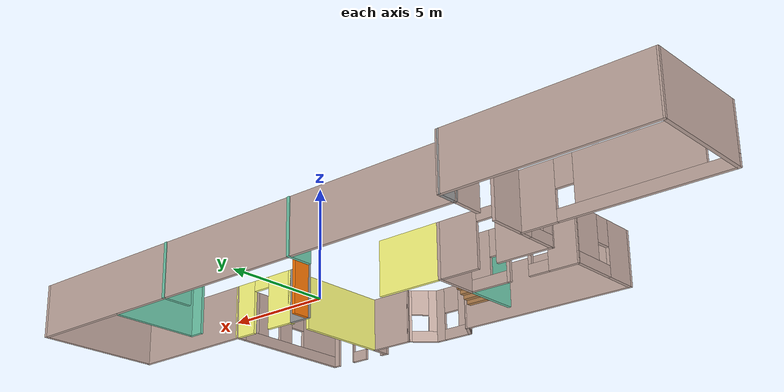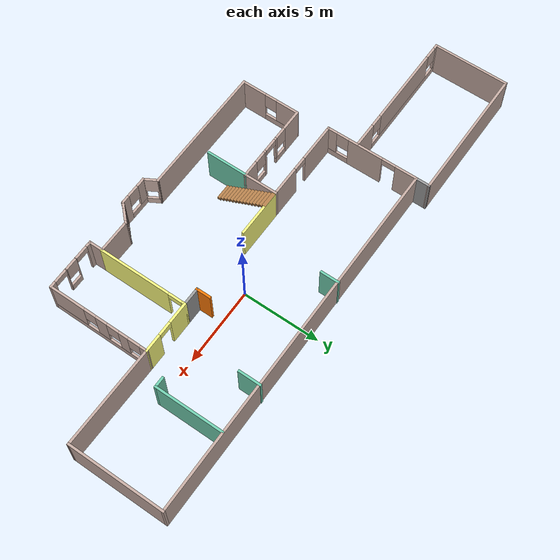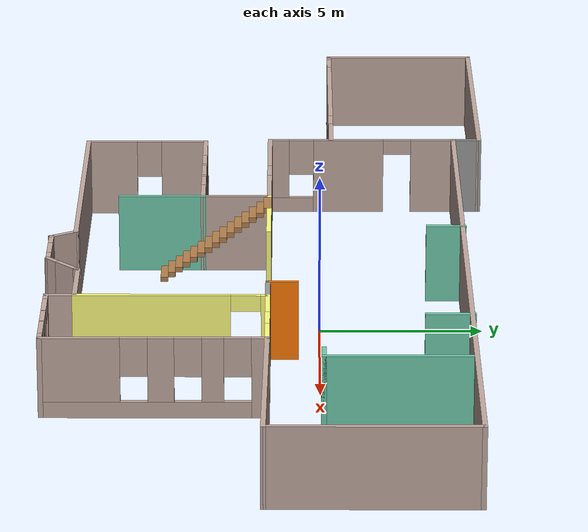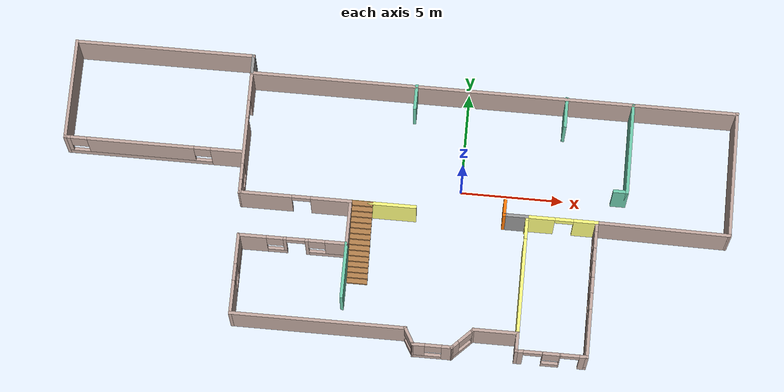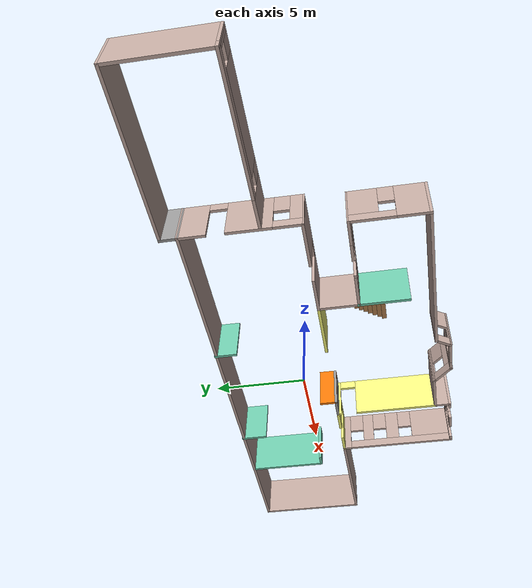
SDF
<?xml version='1.0'?>
<sdf version='1.6'>
  <model name='roboHouse'>
    <pose frame=''>-3.13444 -1.49025 0 0 -0 0</pose>
    <link name='Stairs_0'>
      <visual name='Stairs_0_Visual_0'>
        <pose frame=''>-1.50756 -3.39009 0.083333 0 -0 -3.14159</pose>
        <geometry>
          <box>
            <size>1 0.233333 0.166667</size>
          </box>
        </geometry>
        <material>
          <script>
            <uri>file://media/materials/scripts/gazebo.material</uri>
            <name>Gazebo/Wood</name>
          </script>
          <ambient>0.760784 0.662745 0.627451 1</ambient>
        </material>
        <meta>
          <layer>0</layer>
        </meta>
      </visual>
      <collision name='Stairs_0_Collision_0'>
        <geometry>
          <box>
            <size>1 0.233333 0.166667</size>
          </box>
        </geometry>
        <pose frame=''>-1.50756 -3.39009 0.083333 0 -0 -3.14159</pose>
      </collision>
      <visual name='Stairs_0_Visual_1'>
        <pose frame=''>-1.50756 -3.15675 0.25 0 -0 -3.14159</pose>
        <geometry>
          <box>
            <size>1 0.233333 0.166667</size>
          </box>
        </geometry>
        <material>
          <script>
            <uri>file://media/materials/scripts/gazebo.material</uri>
            <name>Gazebo/Wood</name>
          </script>
          <ambient>0.760784 0.662745 0.627451 1</ambient>
        </material>
        <meta>
          <layer>0</layer>
        </meta>
      </visual>
      <collision name='Stairs_0_Collision_1'>
        <geometry>
          <box>
            <size>1 0.233333 0.166667</size>
          </box>
        </geometry>
        <pose frame=''>-1.50756 -3.15675 0.25 0 -0 -3.14159</pose>
      </collision>
      <visual name='Stairs_0_Visual_2'>
        <pose frame=''>-1.50756 -2.92342 0.416667 0 -0 -3.14159</pose>
        <geometry>
          <box>
            <size>1 0.233333 0.166667</size>
          </box>
        </geometry>
        <material>
          <script>
            <uri>file://media/materials/scripts/gazebo.material</uri>
            <name>Gazebo/Wood</name>
          </script>
          <ambient>0.760784 0.662745 0.627451 1</ambient>
        </material>
        <meta>
          <layer>0</layer>
        </meta>
      </visual>
      <collision name='Stairs_0_Collision_2'>
        <geometry>
          <box>
            <size>1 0.233333 0.166667</size>
          </box>
        </geometry>
        <pose frame=''>-1.50756 -2.92342 0.416667 0 -0 -3.14159</pose>
      </collision>
      <visual name='Stairs_0_Visual_3'>
        <pose frame=''>-1.50756 -2.69009 0.583333 0 -0 -3.14159</pose>
        <geometry>
          <box>
            <size>1 0.233333 0.166667</size>
          </box>
        </geometry>
        <material>
          <script>
            <uri>file://media/materials/scripts/gazebo.material</uri>
            <name>Gazebo/Wood</name>
          </script>
          <ambient>0.760784 0.662745 0.627451 1</ambient>
        </material>
        <meta>
          <layer>0</layer>
        </meta>
      </visual>
      <collision name='Stairs_0_Collision_3'>
        <geometry>
          <box>
            <size>1 0.233333 0.166667</size>
          </box>
        </geometry>
        <pose frame=''>-1.50756 -2.69009 0.583333 0 -0 -3.14159</pose>
      </collision>
      <visual name='Stairs_0_Visual_4'>
        <pose frame=''>-1.50756 -2.45675 0.75 0 -0 -3.14159</pose>
        <geometry>
          <box>
            <size>1 0.233333 0.166667</size>
          </box>
        </geometry>
        <material>
          <script>
            <uri>file://media/materials/scripts/gazebo.material</uri>
            <name>Gazebo/Wood</name>
          </script>
          <ambient>0.760784 0.662745 0.627451 1</ambient>
        </material>
        <meta>
          <layer>0</layer>
        </meta>
      </visual>
      <collision name='Stairs_0_Collision_4'>
        <geometry>
          <box>
            <size>1 0.233333 0.166667</size>
          </box>
        </geometry>
        <pose frame=''>-1.50756 -2.45675 0.75 0 -0 -3.14159</pose>
      </collision>
      <visual name='Stairs_0_Visual_5'>
        <pose frame=''>-1.50756 -2.22342 0.916667 0 -0 -3.14159</pose>
        <geometry>
          <box>
            <size>1 0.233333 0.166667</size>
          </box>
        </geometry>
        <material>
          <script>
            <uri>file://media/materials/scripts/gazebo.material</uri>
            <name>Gazebo/Wood</name>
          </script>
          <ambient>0.760784 0.662745 0.627451 1</ambient>
        </material>
        <meta>
          <layer>0</layer>
        </meta>
      </visual>
      <collision name='Stairs_0_Collision_5'>
        <geometry>
          <box>
            <size>1 0.233333 0.166667</size>
          </box>
        </geometry>
        <pose frame=''>-1.50756 -2.22342 0.916667 0 -0 -3.14159</pose>
      </collision>
      <visual name='Stairs_0_Visual_6'>
        <pose frame=''>-1.50756 -1.99009 1.08333 0 -0 -3.14159</pose>
        <geometry>
          <box>
            <size>1 0.233333 0.166667</size>
          </box>
        </geometry>
        <material>
          <script>
            <uri>file://media/materials/scripts/gazebo.material</uri>
            <name>Gazebo/Wood</name>
          </script>
          <ambient>0.760784 0.662745 0.627451 1</ambient>
        </material>
        <meta>
          <layer>0</layer>
        </meta>
      </visual>
      <collision name='Stairs_0_Collision_6'>
        <geometry>
          <box>
            <size>1 0.233333 0.166667</size>
          </box>
        </geometry>
        <pose frame=''>-1.50756 -1.99009 1.08333 0 -0 -3.14159</pose>
      </collision>
      <visual name='Stairs_0_Visual_7'>
        <pose frame=''>-1.50756 -1.75675 1.25 0 -0 -3.14159</pose>
        <geometry>
          <box>
            <size>1 0.233333 0.166667</size>
          </box>
        </geometry>
        <material>
          <script>
            <uri>file://media/materials/scripts/gazebo.material</uri>
            <name>Gazebo/Wood</name>
          </script>
          <ambient>0.760784 0.662745 0.627451 1</ambient>
        </material>
        <meta>
          <layer>0</layer>
        </meta>
      </visual>
      <collision name='Stairs_0_Collision_7'>
        <geometry>
          <box>
            <size>1 0.233333 0.166667</size>
          </box>
        </geometry>
        <pose frame=''>-1.50756 -1.75675 1.25 0 -0 -3.14159</pose>
      </collision>
      <visual name='Stairs_0_Visual_8'>
        <pose frame=''>-1.50756 -1.52342 1.41667 0 -0 -3.14159</pose>
        <geometry>
          <box>
            <size>1 0.233333 0.166667</size>
          </box>
        </geometry>
        <material>
          <script>
            <uri>file://media/materials/scripts/gazebo.material</uri>
            <name>Gazebo/Wood</name>
          </script>
          <ambient>0.760784 0.662745 0.627451 1</ambient>
        </material>
        <meta>
          <layer>0</layer>
        </meta>
      </visual>
      <collision name='Stairs_0_Collision_8'>
        <geometry>
          <box>
            <size>1 0.233333 0.166667</size>
          </box>
        </geometry>
        <pose frame=''>-1.50756 -1.52342 1.41667 0 -0 -3.14159</pose>
      </collision>
      <visual name='Stairs_0_Visual_9'>
        <pose frame=''>-1.50756 -1.29009 1.58333 0 -0 -3.14159</pose>
        <geometry>
          <box>
            <size>1 0.233333 0.166667</size>
          </box>
        </geometry>
        <material>
          <script>
            <uri>file://media/materials/scripts/gazebo.material</uri>
            <name>Gazebo/Wood</name>
          </script>
          <ambient>0.760784 0.662745 0.627451 1</ambient>
        </material>
        <meta>
          <layer>0</layer>
        </meta>
      </visual>
      <collision name='Stairs_0_Collision_9'>
        <geometry>
          <box>
            <size>1 0.233333 0.166667</size>
          </box>
        </geometry>
        <pose frame=''>-1.50756 -1.29009 1.58333 0 -0 -3.14159</pose>
      </collision>
      <visual name='Stairs_0_Visual_10'>
        <pose frame=''>-1.50756 -1.05675 1.75 0 -0 -3.14159</pose>
        <geometry>
          <box>
            <size>1 0.233333 0.166667</size>
          </box>
        </geometry>
        <material>
          <script>
            <uri>file://media/materials/scripts/gazebo.material</uri>
            <name>Gazebo/Wood</name>
          </script>
          <ambient>0.760784 0.662745 0.627451 1</ambient>
        </material>
        <meta>
          <layer>0</layer>
        </meta>
      </visual>
      <collision name='Stairs_0_Collision_10'>
        <geometry>
          <box>
            <size>1 0.233333 0.166667</size>
          </box>
        </geometry>
        <pose frame=''>-1.50756 -1.05675 1.75 0 -0 -3.14159</pose>
      </collision>
      <visual name='Stairs_0_Visual_11'>
        <pose frame=''>-1.50756 -0.823421 1.91667 0 -0 -3.14159</pose>
        <geometry>
          <box>
            <size>1 0.233333 0.166667</size>
          </box>
        </geometry>
        <material>
          <script>
            <uri>file://media/materials/scripts/gazebo.material</uri>
            <name>Gazebo/Wood</name>
          </script>
          <ambient>0.760784 0.662745 0.627451 1</ambient>
        </material>
        <meta>
          <layer>0</layer>
        </meta>
      </visual>
      <collision name='Stairs_0_Collision_11'>
        <geometry>
          <box>
            <size>1 0.233333 0.166667</size>
          </box>
        </geometry>
        <pose frame=''>-1.50756 -0.823421 1.91667 0 -0 -3.14159</pose>
      </collision>
      <visual name='Stairs_0_Visual_12'>
        <pose frame=''>-1.50756 -0.590088 2.08333 0 -0 -3.14159</pose>
        <geometry>
          <box>
            <size>1 0.233333 0.166667</size>
          </box>
        </geometry>
        <material>
          <script>
            <uri>file://media/materials/scripts/gazebo.material</uri>
            <name>Gazebo/Wood</name>
          </script>
          <ambient>0.760784 0.662745 0.627451 1</ambient>
        </material>
        <meta>
          <layer>0</layer>
        </meta>
      </visual>
      <collision name='Stairs_0_Collision_12'>
        <geometry>
          <box>
            <size>1 0.233333 0.166667</size>
          </box>
        </geometry>
        <pose frame=''>-1.50756 -0.590088 2.08333 0 -0 -3.14159</pose>
      </collision>
      <visual name='Stairs_0_Visual_13'>
        <pose frame=''>-1.50756 -0.356754 2.25 0 -0 -3.14159</pose>
        <geometry>
          <box>
            <size>1 0.233333 0.166667</size>
          </box>
        </geometry>
        <material>
          <script>
            <uri>file://media/materials/scripts/gazebo.material</uri>
            <name>Gazebo/Wood</name>
          </script>
          <ambient>0.760784 0.662745 0.627451 1</ambient>
        </material>
        <meta>
          <layer>0</layer>
        </meta>
      </visual>
      <collision name='Stairs_0_Collision_13'>
        <geometry>
          <box>
            <size>1 0.233333 0.166667</size>
          </box>
        </geometry>
        <pose frame=''>-1.50756 -0.356754 2.25 0 -0 -3.14159</pose>
      </collision>
      <visual name='Stairs_0_Visual_14'>
        <pose frame=''>-1.50756 -0.123421 2.41667 0 -0 -3.14159</pose>
        <geometry>
          <box>
            <size>1 0.233333 0.166667</size>
          </box>
        </geometry>
        <material>
          <script>
            <uri>file://media/materials/scripts/gazebo.material</uri>
            <name>Gazebo/Wood</name>
          </script>
          <ambient>0.760784 0.662745 0.627451 1</ambient>
        </material>
        <meta>
          <layer>0</layer>
        </meta>
      </visual>
      <collision name='Stairs_0_Collision_14'>
        <geometry>
          <box>
            <size>1 0.233333 0.166667</size>
          </box>
        </geometry>
        <pose frame=''>-1.50756 -0.123421 2.41667 0 -0 -3.14159</pose>
      </collision>
    </link>
    <link name='Wall_1'>
      <pose frame=''>9.75444 -3.36976 0 0 0 -1.5708</pose>
      <visual name='Wall_1_Visual_0'>
        <pose frame=''>-3.11075 0 1.25 0 -0 0</pose>
        <geometry>
          <box>
            <size>0.5285 0.15 2.5</size>
          </box>
        </geometry>
        <material>
          <script>
            <uri>file://media/materials/scripts/gazebo.material</uri>
            <name>Gazebo/Grey</name>
          </script>
          <ambient>0.760784 0.662745 0.627451 1</ambient>
        </material>
        <meta>
          <layer>0</layer>
        </meta>
      </visual>
      <collision name='Wall_1_Collision_0'>
        <geometry>
          <box>
            <size>0.5285 0.15 2.5</size>
          </box>
        </geometry>
        <pose frame=''>-3.11075 0 1.25 0 -0 0</pose>
      </collision>
      <visual name='Wall_1_Visual_1'>
        <pose frame=''>0.26425 0 0.25 0 -0 0</pose>
        <geometry>
          <box>
            <size>6.2215 0.15 0.5</size>
          </box>
        </geometry>
        <material>
          <script>
            <uri>file://media/materials/scripts/gazebo.material</uri>
            <name>Gazebo/Grey</name>
          </script>
          <ambient>0.760784 0.662745 0.627451 1</ambient>
        </material>
        <meta>
          <layer>0</layer>
        </meta>
      </visual>
      <collision name='Wall_1_Collision_1'>
        <geometry>
          <box>
            <size>6.2215 0.15 0.5</size>
          </box>
        </geometry>
        <pose frame=''>0.26425 0 0.25 0 -0 0</pose>
      </collision>
      <visual name='Wall_1_Visual_2'>
        <pose frame=''>-1.72468 0 1.5 0 -0 0</pose>
        <geometry>
          <box>
            <size>0.643636 0.15 2</size>
          </box>
        </geometry>
        <material>
          <script>
            <uri>file://media/materials/scripts/gazebo.material</uri>
            <name>Gazebo/Grey</name>
          </script>
          <ambient>0.760784 0.662745 0.627451 1</ambient>
        </material>
        <meta>
          <layer>0</layer>
        </meta>
      </visual>
      <collision name='Wall_1_Collision_2'>
        <geometry>
          <box>
            <size>0.643636 0.15 2</size>
          </box>
        </geometry>
        <pose frame=''>-1.72468 0 1.5 0 -0 0</pose>
      </collision>
      <visual name='Wall_1_Visual_3'>
        <pose frame=''>-0.215811 0 1.5 0 -0 0</pose>
        <geometry>
          <box>
            <size>0.774106 0.15 2</size>
          </box>
        </geometry>
        <material>
          <script>
            <uri>file://media/materials/scripts/gazebo.material</uri>
            <name>Gazebo/Grey</name>
          </script>
          <ambient>0.760784 0.662745 0.627451 1</ambient>
        </material>
        <meta>
          <layer>0</layer>
        </meta>
      </visual>
      <collision name='Wall_1_Collision_3'>
        <geometry>
          <box>
            <size>0.774106 0.15 2</size>
          </box>
        </geometry>
        <pose frame=''>-0.215811 0 1.5 0 -0 0</pose>
      </collision>
      <visual name='Wall_1_Visual_4'>
        <pose frame=''>2.17312 0 1.5 0 -0 0</pose>
        <geometry>
          <box>
            <size>2.40376 0.15 2</size>
          </box>
        </geometry>
        <material>
          <script>
            <uri>file://media/materials/scripts/gazebo.material</uri>
            <name>Gazebo/Grey</name>
          </script>
          <ambient>0.760784 0.662745 0.627451 1</ambient>
        </material>
        <meta>
          <layer>0</layer>
        </meta>
      </visual>
      <collision name='Wall_1_Collision_4'>
        <geometry>
          <box>
            <size>2.40376 0.15 2</size>
          </box>
        </geometry>
        <pose frame=''>2.17312 0 1.5 0 -0 0</pose>
      </collision>
      <visual name='Wall_1_Visual_5'>
        <pose frame=''>-2.4465 0 1.9 0 -0 0</pose>
        <geometry>
          <box>
            <size>0.8 0.15 1.2</size>
          </box>
        </geometry>
        <material>
          <script>
            <uri>file://media/materials/scripts/gazebo.material</uri>
            <name>Gazebo/Grey</name>
          </script>
          <ambient>0.760784 0.662745 0.627451 1</ambient>
        </material>
        <meta>
          <layer>0</layer>
        </meta>
      </visual>
      <collision name='Wall_1_Collision_5'>
        <geometry>
          <box>
            <size>0.8 0.15 1.2</size>
          </box>
        </geometry>
        <pose frame=''>-2.4465 0 1.9 0 -0 0</pose>
      </collision>
      <visual name='Wall_1_Visual_6'>
        <pose frame=''>-1.00286 0 1.9 0 -0 0</pose>
        <geometry>
          <box>
            <size>0.8 0.15 1.2</size>
          </box>
        </geometry>
        <material>
          <script>
            <uri>file://media/materials/scripts/gazebo.material</uri>
            <name>Gazebo/Grey</name>
          </script>
          <ambient>0.760784 0.662745 0.627451 1</ambient>
        </material>
        <meta>
          <layer>0</layer>
        </meta>
      </visual>
      <collision name='Wall_1_Collision_6'>
        <geometry>
          <box>
            <size>0.8 0.15 1.2</size>
          </box>
        </geometry>
        <pose frame=''>-1.00286 0 1.9 0 -0 0</pose>
      </collision>
      <visual name='Wall_1_Visual_7'>
        <pose frame=''>0.571241 0 1.9 0 -0 0</pose>
        <geometry>
          <box>
            <size>0.8 0.15 1.2</size>
          </box>
        </geometry>
        <material>
          <script>
            <uri>file://media/materials/scripts/gazebo.material</uri>
            <name>Gazebo/Grey</name>
          </script>
          <ambient>0.760784 0.662745 0.627451 1</ambient>
        </material>
        <meta>
          <layer>0</layer>
        </meta>
      </visual>
      <collision name='Wall_1_Collision_7'>
        <geometry>
          <box>
            <size>0.8 0.15 1.2</size>
          </box>
        </geometry>
        <pose frame=''>0.571241 0 1.9 0 -0 0</pose>
      </collision>
    </link>
    <link name='Wall_10'>
      <pose frame=''>-4.68535 -2.17899 0 0 -0 0.003566</pose>
      <visual name='Wall_10_Visual_0'>
        <pose frame=''>-1.95766 0 1.25 0 -0 0</pose>
        <geometry>
          <box>
            <size>1.4143 0.15 2.5</size>
          </box>
        </geometry>
        <material>
          <script>
            <uri>file://media/materials/scripts/gazebo.material</uri>
            <name>Gazebo/Grey</name>
          </script>
          <ambient>0.760784 0.662745 0.627451 1</ambient>
        </material>
        <meta>
          <layer>0</layer>
        </meta>
      </visual>
      <collision name='Wall_10_Collision_0'>
        <geometry>
          <box>
            <size>1.4143 0.15 2.5</size>
          </box>
        </geometry>
        <pose frame=''>-1.95766 0 1.25 0 -0 0</pose>
      </collision>
      <visual name='Wall_10_Visual_1'>
        <pose frame=''>0.68156 0 1.25 0 -0 0</pose>
        <geometry>
          <box>
            <size>0.155471 0.15 2.5</size>
          </box>
        </geometry>
        <material>
          <script>
            <uri>file://media/materials/scripts/gazebo.material</uri>
            <name>Gazebo/Grey</name>
          </script>
          <ambient>0.760784 0.662745 0.627451 1</ambient>
        </material>
        <meta>
          <layer>0</layer>
        </meta>
      </visual>
      <collision name='Wall_10_Collision_1'>
        <geometry>
          <box>
            <size>0.155471 0.15 2.5</size>
          </box>
        </geometry>
        <pose frame=''>0.68156 0 1.25 0 -0 0</pose>
      </collision>
      <visual name='Wall_10_Visual_2'>
        <pose frame=''>-0.773344 0 0.25 0 -0 0</pose>
        <geometry>
          <box>
            <size>0.954338 0.15 0.5</size>
          </box>
        </geometry>
        <material>
          <script>
            <uri>file://media/materials/scripts/gazebo.material</uri>
            <name>Gazebo/Grey</name>
          </script>
          <ambient>0.760784 0.662745 0.627451 1</ambient>
        </material>
        <meta>
          <layer>0</layer>
        </meta>
      </visual>
      <collision name='Wall_10_Collision_2'>
        <geometry>
          <box>
            <size>0.954338 0.15 0.5</size>
          </box>
        </geometry>
        <pose frame=''>-0.773344 0 0.25 0 -0 0</pose>
      </collision>
      <visual name='Wall_10_Visual_3'>
        <pose frame=''>1.71206 0 0.25 0 -0 0</pose>
        <geometry>
          <box>
            <size>1.90552 0.15 0.5</size>
          </box>
        </geometry>
        <material>
          <script>
            <uri>file://media/materials/scripts/gazebo.material</uri>
            <name>Gazebo/Grey</name>
          </script>
          <ambient>0.760784 0.662745 0.627451 1</ambient>
        </material>
        <meta>
          <layer>0</layer>
        </meta>
      </visual>
      <collision name='Wall_10_Collision_3'>
        <geometry>
          <box>
            <size>1.90552 0.15 0.5</size>
          </box>
        </geometry>
        <pose frame=''>1.71206 0 0.25 0 -0 0</pose>
      </collision>
      <visual name='Wall_10_Visual_4'>
        <pose frame=''>-0.373344 0 1.5 0 -0 0</pose>
        <geometry>
          <box>
            <size>0.154338 0.15 2</size>
          </box>
        </geometry>
        <material>
          <script>
            <uri>file://media/materials/scripts/gazebo.material</uri>
            <name>Gazebo/Grey</name>
          </script>
          <ambient>0.760784 0.662745 0.627451 1</ambient>
        </material>
        <meta>
          <layer>0</layer>
        </meta>
      </visual>
      <collision name='Wall_10_Collision_4'>
        <geometry>
          <box>
            <size>0.154338 0.15 2</size>
          </box>
        </geometry>
        <pose frame=''>-0.373344 0 1.5 0 -0 0</pose>
      </collision>
      <visual name='Wall_10_Visual_5'>
        <pose frame=''>-0.373344 0 1.5 0 -0 0</pose>
        <geometry>
          <box>
            <size>0.154338 0.15 2</size>
          </box>
        </geometry>
        <material>
          <script>
            <uri>file://media/materials/scripts/gazebo.material</uri>
            <name>Gazebo/Grey</name>
          </script>
          <ambient>0.760784 0.662745 0.627451 1</ambient>
        </material>
        <meta>
          <layer>0</layer>
        </meta>
      </visual>
      <collision name='Wall_10_Collision_5'>
        <geometry>
          <box>
            <size>0.154338 0.15 2</size>
          </box>
        </geometry>
        <pose frame=''>-0.373344 0 1.5 0 -0 0</pose>
      </collision>
      <visual name='Wall_10_Visual_6'>
        <pose frame=''>2.11205 0 1.5 0 -0 0</pose>
        <geometry>
          <box>
            <size>1.10552 0.15 2</size>
          </box>
        </geometry>
        <material>
          <script>
            <uri>file://media/materials/scripts/gazebo.material</uri>
            <name>Gazebo/Grey</name>
          </script>
          <ambient>0.760784 0.662745 0.627451 1</ambient>
        </material>
        <meta>
          <layer>0</layer>
        </meta>
      </visual>
      <collision name='Wall_10_Collision_6'>
        <geometry>
          <box>
            <size>1.10552 0.15 2</size>
          </box>
        </geometry>
        <pose frame=''>2.11205 0 1.5 0 -0 0</pose>
      </collision>
      <visual name='Wall_10_Visual_7'>
        <pose frame=''>-0.850514 0 1.9 0 -0 0</pose>
        <geometry>
          <box>
            <size>0.8 0.15 1.2</size>
          </box>
        </geometry>
        <material>
          <script>
            <uri>file://media/materials/scripts/gazebo.material</uri>
            <name>Gazebo/Grey</name>
          </script>
          <ambient>0.760784 0.662745 0.627451 1</ambient>
        </material>
        <meta>
          <layer>0</layer>
        </meta>
      </visual>
      <collision name='Wall_10_Collision_7'>
        <geometry>
          <box>
            <size>0.8 0.15 1.2</size>
          </box>
        </geometry>
        <pose frame=''>-0.850514 0 1.9 0 -0 0</pose>
      </collision>
      <visual name='Wall_10_Visual_8'>
        <pose frame=''>1.1593 0 1.9 0 -0 0</pose>
        <geometry>
          <box>
            <size>0.8 0.15 1.2</size>
          </box>
        </geometry>
        <material>
          <script>
            <uri>file://media/materials/scripts/gazebo.material</uri>
            <name>Gazebo/Grey</name>
          </script>
          <ambient>0.760784 0.662745 0.627451 1</ambient>
        </material>
        <meta>
          <layer>0</layer>
        </meta>
      </visual>
      <collision name='Wall_10_Collision_8'>
        <geometry>
          <box>
            <size>0.8 0.15 1.2</size>
          </box>
        </geometry>
        <pose frame=''>1.1593 0 1.9 0 -0 0</pose>
      </collision>
      <visual name='Wall_10_Visual_9'>
        <pose frame=''>0.153825 0 2.25 0 -0 0</pose>
        <geometry>
          <box>
            <size>0.9 0.15 0.5</size>
          </box>
        </geometry>
        <material>
          <script>
            <uri>file://media/materials/scripts/gazebo.material</uri>
            <name>Gazebo/Grey</name>
          </script>
          <ambient>0.760784 0.662745 0.627451 1</ambient>
        </material>
        <meta>
          <layer>0</layer>
        </meta>
      </visual>
      <collision name='Wall_10_Collision_9'>
        <geometry>
          <box>
            <size>0.9 0.15 0.5</size>
          </box>
        </geometry>
        <pose frame=''>0.153825 0 2.25 0 -0 0</pose>
      </collision>
      <visual name='Wall_10_Visual_10'>
        <pose frame=''>0.153825 0 2.25 0 -0 0</pose>
        <geometry>
          <box>
            <size>0.9 0.15 0.5</size>
          </box>
        </geometry>
        <material>
          <script>
            <uri>file://media/materials/scripts/gazebo.material</uri>
            <name>Gazebo/Grey</name>
          </script>
          <ambient>0.760784 0.662745 0.627451 1</ambient>
        </material>
        <meta>
          <layer>0</layer>
        </meta>
      </visual>
      <collision name='Wall_10_Collision_10'>
        <geometry>
          <box>
            <size>0.9 0.15 0.5</size>
          </box>
        </geometry>
        <pose frame=''>0.153825 0 2.25 0 -0 0</pose>
      </collision>
    </link>
    <link name='Wall_11'>
      <collision name='Wall_11_Collision'>
        <geometry>
          <box>
            <size>2.25 0.15 2.5</size>
          </box>
        </geometry>
        <pose frame=''>0 0 1.25 0 -0 0</pose>
      </collision>
      <visual name='Wall_11_Visual'>
        <pose frame=''>0 0 1.25 0 -0 0</pose>
        <geometry>
          <box>
            <size>2.25 0.15 2.5</size>
          </box>
        </geometry>
        <material>
          <script>
            <uri>file://media/materials/scripts/gazebo.material</uri>
            <name>Gazebo/Grey</name>
          </script>
          <ambient>0.760784 0.662745 0.627451 1</ambient>
        </material>
        <meta>
          <layer>0</layer>
        </meta>
      </visual>
      <pose frame=''>-2.09556 -1.11975 0 0 -0 1.5708</pose>
    </link>
    <link name='Wall_13'>
      <collision name='Wall_13_Collision'>
        <geometry>
          <box>
            <size>6.51573 0.15 2.5</size>
          </box>
        </geometry>
        <pose frame=''>0 0 1.25 0 -0 0</pose>
      </collision>
      <visual name='Wall_13_Visual'>
        <pose frame=''>0 0 1.25 0 -0 0</pose>
        <geometry>
          <box>
            <size>6.51573 0.15 2.5</size>
          </box>
        </geometry>
        <material>
          <script>
            <uri>file://media/materials/scripts/gazebo.material</uri>
            <name>Gazebo/Grey</name>
          </script>
          <ambient>0.760784 0.662745 0.627451 1</ambient>
        </material>
        <meta>
          <layer>0</layer>
        </meta>
      </visual>
      <pose frame=''>12.9371 -0.107254 0 0 0 -0.011782</pose>
    </link>
    <link name='Wall_14'>
      <collision name='Wall_14_Collision'>
        <geometry>
          <box>
            <size>6.25 0.15 2.5</size>
          </box>
        </geometry>
        <pose frame=''>0 0 1.25 0 -0 0</pose>
      </collision>
      <visual name='Wall_14_Visual'>
        <pose frame=''>0 0 1.25 0 -0 0</pose>
        <geometry>
          <box>
            <size>6.25 0.15 2.5</size>
          </box>
        </geometry>
        <material>
          <script>
            <uri>file://media/materials/scripts/gazebo.material</uri>
            <name>Gazebo/Grey</name>
          </script>
          <ambient>0.760784 0.662745 0.627451 1</ambient>
        </material>
        <meta>
          <layer>0</layer>
        </meta>
      </visual>
      <pose frame=''>16.1197 2.90525 0 0 -0 1.5708</pose>
    </link>
    <link name='Wall_15'>
      <collision name='Wall_15_Collision'>
        <geometry>
          <box>
            <size>23.75 0.15 2.5</size>
          </box>
        </geometry>
        <pose frame=''>0 0 1.25 0 -0 0</pose>
      </collision>
      <visual name='Wall_15_Visual'>
        <pose frame=''>0 0 1.25 0 -0 0</pose>
        <geometry>
          <box>
            <size>23.75 0.15 2.5</size>
          </box>
        </geometry>
        <material>
          <script>
            <uri>file://media/materials/scripts/gazebo.material</uri>
            <name>Gazebo/Grey</name>
          </script>
          <ambient>0.760784 0.662745 0.627451 1</ambient>
        </material>
        <meta>
          <layer>0</layer>
        </meta>
      </visual>
      <pose frame=''>4.31973 5.95525 0 0 -0 3.14159</pose>
    </link>
    <link name='Wall_16'>
      <pose frame=''>-7.46291 2.94275 0 0 0 -1.56503</pose>
      <visual name='Wall_16_Visual_0'>
        <pose frame=''>-2.34957 0 1.25 0 -0 0</pose>
        <geometry>
          <box>
            <size>1.47595 0.15 2.5</size>
          </box>
        </geometry>
        <material>
          <script>
            <uri>file://media/materials/scripts/gazebo.material</uri>
            <name>Gazebo/Grey</name>
          </script>
          <ambient>0.760784 0.662745 0.627451 1</ambient>
        </material>
        <meta>
          <layer>0</layer>
        </meta>
      </visual>
      <collision name='Wall_16_Collision_0'>
        <geometry>
          <box>
            <size>1.47595 0.15 2.5</size>
          </box>
        </geometry>
        <pose frame=''>-2.34957 0 1.25 0 -0 0</pose>
      </collision>
      <visual name='Wall_16_Visual_1'>
        <pose frame=''>0.43708 0 1.25 0 -0 0</pose>
        <geometry>
          <box>
            <size>2.29735 0.15 2.5</size>
          </box>
        </geometry>
        <material>
          <script>
            <uri>file://media/materials/scripts/gazebo.material</uri>
            <name>Gazebo/Grey</name>
          </script>
          <ambient>0.760784 0.662745 0.627451 1</ambient>
        </material>
        <meta>
          <layer>0</layer>
        </meta>
      </visual>
      <collision name='Wall_16_Collision_1'>
        <geometry>
          <box>
            <size>2.29735 0.15 2.5</size>
          </box>
        </geometry>
        <pose frame=''>0.43708 0 1.25 0 -0 0</pose>
      </collision>
      <visual name='Wall_16_Visual_2'>
        <pose frame=''>2.33665 0 0.25 0 -0 0</pose>
        <geometry>
          <box>
            <size>1.50179 0.15 0.5</size>
          </box>
        </geometry>
        <material>
          <script>
            <uri>file://media/materials/scripts/gazebo.material</uri>
            <name>Gazebo/Grey</name>
          </script>
          <ambient>0.760784 0.662745 0.627451 1</ambient>
        </material>
        <meta>
          <layer>0</layer>
        </meta>
      </visual>
      <collision name='Wall_16_Collision_2'>
        <geometry>
          <box>
            <size>1.50179 0.15 0.5</size>
          </box>
        </geometry>
        <pose frame=''>2.33665 0 0.25 0 -0 0</pose>
      </collision>
      <visual name='Wall_16_Visual_3'>
        <pose frame=''>2.73665 0 1.5 0 -0 0</pose>
        <geometry>
          <box>
            <size>0.701794 0.15 2</size>
          </box>
        </geometry>
        <material>
          <script>
            <uri>file://media/materials/scripts/gazebo.material</uri>
            <name>Gazebo/Grey</name>
          </script>
          <ambient>0.760784 0.662745 0.627451 1</ambient>
        </material>
        <meta>
          <layer>0</layer>
        </meta>
      </visual>
      <collision name='Wall_16_Collision_3'>
        <geometry>
          <box>
            <size>0.701794 0.15 2</size>
          </box>
        </geometry>
        <pose frame=''>2.73665 0 1.5 0 -0 0</pose>
      </collision>
      <visual name='Wall_16_Visual_4'>
        <pose frame=''>1.98576 0 1.9 0 -0 0</pose>
        <geometry>
          <box>
            <size>0.8 0.15 1.2</size>
          </box>
        </geometry>
        <material>
          <script>
            <uri>file://media/materials/scripts/gazebo.material</uri>
            <name>Gazebo/Grey</name>
          </script>
          <ambient>0.760784 0.662745 0.627451 1</ambient>
        </material>
        <meta>
          <layer>0</layer>
        </meta>
      </visual>
      <collision name='Wall_16_Collision_4'>
        <geometry>
          <box>
            <size>0.8 0.15 1.2</size>
          </box>
        </geometry>
        <pose frame=''>1.98576 0 1.9 0 -0 0</pose>
      </collision>
      <visual name='Wall_16_Visual_5'>
        <pose frame=''>-1.1616 0 2.25 0 -0 0</pose>
        <geometry>
          <box>
            <size>0.9 0.15 0.5</size>
          </box>
        </geometry>
        <material>
          <script>
            <uri>file://media/materials/scripts/gazebo.material</uri>
            <name>Gazebo/Grey</name>
          </script>
          <ambient>0.760784 0.662745 0.627451 1</ambient>
        </material>
        <meta>
          <layer>0</layer>
        </meta>
      </visual>
      <collision name='Wall_16_Collision_5'>
        <geometry>
          <box>
            <size>0.9 0.15 0.5</size>
          </box>
        </geometry>
        <pose frame=''>-1.1616 0 2.25 0 -0 0</pose>
      </collision>
    </link>
    <link name='Wall_17'>
      <pose frame=''>-4.77056 -0.069754 0 0 -0 0</pose>
      <visual name='Wall_17_Visual_0'>
        <pose frame=''>-1.45331 0 1.25 0 -0 0</pose>
        <geometry>
          <box>
            <size>2.59339 0.15 2.5</size>
          </box>
        </geometry>
        <material>
          <script>
            <uri>file://media/materials/scripts/gazebo.material</uri>
            <name>Gazebo/Grey</name>
          </script>
          <ambient>0.760784 0.662745 0.627451 1</ambient>
        </material>
        <meta>
          <layer>0</layer>
        </meta>
      </visual>
      <collision name='Wall_17_Collision_0'>
        <geometry>
          <box>
            <size>2.59339 0.15 2.5</size>
          </box>
        </geometry>
        <pose frame=''>-1.45331 0 1.25 0 -0 0</pose>
      </collision>
      <visual name='Wall_17_Visual_1'>
        <pose frame=''>1.7467 0 1.25 0 -0 0</pose>
        <geometry>
          <box>
            <size>2.00661 0.15 2.5</size>
          </box>
        </geometry>
        <material>
          <script>
            <uri>file://media/materials/scripts/gazebo.material</uri>
            <name>Gazebo/Grey</name>
          </script>
          <ambient>0.760784 0.662745 0.627451 1</ambient>
        </material>
        <meta>
          <layer>0</layer>
        </meta>
      </visual>
      <collision name='Wall_17_Collision_1'>
        <geometry>
          <box>
            <size>2.00661 0.15 2.5</size>
          </box>
        </geometry>
        <pose frame=''>1.7467 0 1.25 0 -0 0</pose>
      </collision>
      <visual name='Wall_17_Visual_2'>
        <pose frame=''>0.29339 0 2.25 0 -0 0</pose>
        <geometry>
          <box>
            <size>0.9 0.15 0.5</size>
          </box>
        </geometry>
        <material>
          <script>
            <uri>file://media/materials/scripts/gazebo.material</uri>
            <name>Gazebo/Grey</name>
          </script>
          <ambient>0.760784 0.662745 0.627451 1</ambient>
        </material>
        <meta>
          <layer>0</layer>
        </meta>
      </visual>
      <collision name='Wall_17_Collision_2'>
        <geometry>
          <box>
            <size>0.9 0.15 0.5</size>
          </box>
        </geometry>
        <pose frame=''>0.29339 0 2.25 0 -0 0</pose>
      </collision>
    </link>
    <link name='Wall_19'>
      <pose frame=''>6.40444 -2.94475 0 0 -0 1.5708</pose>
      <visual name='Wall_19_Visual_0'>
        <pose frame=''>-0.589035 0 1.25 0 -0 0</pose>
        <geometry>
          <box>
            <size>4.72193 0.15 2.5</size>
          </box>
        </geometry>
        <material>
          <script>
            <uri>file://media/materials/scripts/gazebo.material</uri>
            <name>Gazebo/Grey</name>
          </script>
          <ambient>1 1 0.498039 1</ambient>
        </material>
        <meta>
          <layer>0</layer>
        </meta>
      </visual>
      <collision name='Wall_19_Collision_0'>
        <geometry>
          <box>
            <size>4.72193 0.15 2.5</size>
          </box>
        </geometry>
        <pose frame=''>-0.589035 0 1.25 0 -0 0</pose>
      </collision>
      <visual name='Wall_19_Visual_1'>
        <pose frame=''>2.81096 0 1.25 0 -0 0</pose>
        <geometry>
          <box>
            <size>0.27807 0.15 2.5</size>
          </box>
        </geometry>
        <material>
          <script>
            <uri>file://media/materials/scripts/gazebo.material</uri>
            <name>Gazebo/Grey</name>
          </script>
          <ambient>1 1 0.498039 1</ambient>
        </material>
        <meta>
          <layer>0</layer>
        </meta>
      </visual>
      <collision name='Wall_19_Collision_1'>
        <geometry>
          <box>
            <size>0.27807 0.15 2.5</size>
          </box>
        </geometry>
        <pose frame=''>2.81096 0 1.25 0 -0 0</pose>
      </collision>
      <visual name='Wall_19_Visual_2'>
        <pose frame=''>2.22193 0 2.25 0 -0 0</pose>
        <geometry>
          <box>
            <size>0.9 0.15 0.5</size>
          </box>
        </geometry>
        <material>
          <script>
            <uri>file://media/materials/scripts/gazebo.material</uri>
            <name>Gazebo/Grey</name>
          </script>
          <ambient>1 1 0.498039 1</ambient>
        </material>
        <meta>
          <layer>0</layer>
        </meta>
      </visual>
      <collision name='Wall_19_Collision_2'>
        <geometry>
          <box>
            <size>0.9 0.15 0.5</size>
          </box>
        </geometry>
        <pose frame=''>2.22193 0 2.25 0 -0 0</pose>
      </collision>
    </link>
    <link name='Wall_2'>
      <pose frame=''>8.07944 -6.66975 0 0 -0 3.14159</pose>
      <visual name='Wall_2_Visual_0'>
        <pose frame=''>-1.539 0 1.25 0 -0 0</pose>
        <geometry>
          <box>
            <size>0.422 0.15 2.5</size>
          </box>
        </geometry>
        <material>
          <script>
            <uri>file://media/materials/scripts/gazebo.material</uri>
            <name>Gazebo/Grey</name>
          </script>
          <ambient>0.760784 0.662745 0.627451 1</ambient>
        </material>
        <meta>
          <layer>0</layer>
        </meta>
      </visual>
      <collision name='Wall_2_Collision_0'>
        <geometry>
          <box>
            <size>0.422 0.15 2.5</size>
          </box>
        </geometry>
        <pose frame=''>-1.539 0 1.25 0 -0 0</pose>
      </collision>
      <visual name='Wall_2_Visual_1'>
        <pose frame=''>-0.403875 0 1.25 0 -0 0</pose>
        <geometry>
          <box>
            <size>0.04825 0.15 2.5</size>
          </box>
        </geometry>
        <material>
          <script>
            <uri>file://media/materials/scripts/gazebo.material</uri>
            <name>Gazebo/Grey</name>
          </script>
          <ambient>0.760784 0.662745 0.627451 1</ambient>
        </material>
        <meta>
          <layer>0</layer>
        </meta>
      </visual>
      <collision name='Wall_2_Collision_1'>
        <geometry>
          <box>
            <size>0.04825 0.15 2.5</size>
          </box>
        </geometry>
        <pose frame=''>-0.403875 0 1.25 0 -0 0</pose>
      </collision>
      <visual name='Wall_2_Visual_2'>
        <pose frame=''>1.54655 0 1.25 0 -0 0</pose>
        <geometry>
          <box>
            <size>0.4069 0.15 2.5</size>
          </box>
        </geometry>
        <material>
          <script>
            <uri>file://media/materials/scripts/gazebo.material</uri>
            <name>Gazebo/Grey</name>
          </script>
          <ambient>0.760784 0.662745 0.627451 1</ambient>
        </material>
        <meta>
          <layer>0</layer>
        </meta>
      </visual>
      <collision name='Wall_2_Collision_2'>
        <geometry>
          <box>
            <size>0.4069 0.15 2.5</size>
          </box>
        </geometry>
        <pose frame=''>1.54655 0 1.25 0 -0 0</pose>
      </collision>
      <visual name='Wall_2_Visual_3'>
        <pose frame=''>0.031675 0 0.25 0 -0 0</pose>
        <geometry>
          <box>
            <size>0.82285 0.15 0.5</size>
          </box>
        </geometry>
        <material>
          <script>
            <uri>file://media/materials/scripts/gazebo.material</uri>
            <name>Gazebo/Grey</name>
          </script>
          <ambient>0.760784 0.662745 0.627451 1</ambient>
        </material>
        <meta>
          <layer>0</layer>
        </meta>
      </visual>
      <collision name='Wall_2_Collision_3'>
        <geometry>
          <box>
            <size>0.82285 0.15 0.5</size>
          </box>
        </geometry>
        <pose frame=''>0.031675 0 0.25 0 -0 0</pose>
      </collision>
      <visual name='Wall_2_Visual_4'>
        <pose frame=''>0.431675 0 1.5 0 -0 0</pose>
        <geometry>
          <box>
            <size>0.02285 0.15 2</size>
          </box>
        </geometry>
        <material>
          <script>
            <uri>file://media/materials/scripts/gazebo.material</uri>
            <name>Gazebo/Grey</name>
          </script>
          <ambient>0.760784 0.662745 0.627451 1</ambient>
        </material>
        <meta>
          <layer>0</layer>
        </meta>
      </visual>
      <collision name='Wall_2_Collision_4'>
        <geometry>
          <box>
            <size>0.02285 0.15 2</size>
          </box>
        </geometry>
        <pose frame=''>0.431675 0 1.5 0 -0 0</pose>
      </collision>
      <visual name='Wall_2_Visual_5'>
        <pose frame=''>0.02025 0 1.9 0 -0 0</pose>
        <geometry>
          <box>
            <size>0.8 0.15 1.2</size>
          </box>
        </geometry>
        <material>
          <script>
            <uri>file://media/materials/scripts/gazebo.material</uri>
            <name>Gazebo/Grey</name>
          </script>
          <ambient>0.760784 0.662745 0.627451 1</ambient>
        </material>
        <meta>
          <layer>0</layer>
        </meta>
      </visual>
      <collision name='Wall_2_Collision_5'>
        <geometry>
          <box>
            <size>0.8 0.15 1.2</size>
          </box>
        </geometry>
        <pose frame=''>0.02025 0 1.9 0 -0 0</pose>
      </collision>
      <visual name='Wall_2_Visual_6'>
        <pose frame=''>-0.878 0 2.25 0 -0 0</pose>
        <geometry>
          <box>
            <size>0.9 0.15 0.5</size>
          </box>
        </geometry>
        <material>
          <script>
            <uri>file://media/materials/scripts/gazebo.material</uri>
            <name>Gazebo/Grey</name>
          </script>
          <ambient>0.760784 0.662745 0.627451 1</ambient>
        </material>
        <meta>
          <layer>0</layer>
        </meta>
      </visual>
      <collision name='Wall_2_Collision_6'>
        <geometry>
          <box>
            <size>0.9 0.15 0.5</size>
          </box>
        </geometry>
        <pose frame=''>-0.878 0 2.25 0 -0 0</pose>
      </collision>
      <visual name='Wall_2_Visual_7'>
        <pose frame=''>0.8931 0 2.25 0 -0 0</pose>
        <geometry>
          <box>
            <size>0.9 0.15 0.5</size>
          </box>
        </geometry>
        <material>
          <script>
            <uri>file://media/materials/scripts/gazebo.material</uri>
            <name>Gazebo/Grey</name>
          </script>
          <ambient>0.760784 0.662745 0.627451 1</ambient>
        </material>
        <meta>
          <layer>0</layer>
        </meta>
      </visual>
      <collision name='Wall_2_Collision_7'>
        <geometry>
          <box>
            <size>0.9 0.15 0.5</size>
          </box>
        </geometry>
        <pose frame=''>0.8931 0 2.25 0 -0 0</pose>
      </collision>
    </link>
    <link name='Wall_20'>
      <pose frame=''>8.07944 -0.069754 0 0 -0 0</pose>
      <visual name='Wall_20_Visual_0'>
        <pose frame=''>-1.0469 0 1.25 0 -0 0</pose>
        <geometry>
          <box>
            <size>1.4062 0.15 2.5</size>
          </box>
        </geometry>
        <material>
          <script>
            <uri>file://media/materials/scripts/gazebo.material</uri>
            <name>Gazebo/Grey</name>
          </script>
          <ambient>1 1 0.498039 1</ambient>
        </material>
        <meta>
          <layer>0</layer>
        </meta>
      </visual>
      <collision name='Wall_20_Collision_0'>
        <geometry>
          <box>
            <size>1.4062 0.15 2.5</size>
          </box>
        </geometry>
        <pose frame=''>-1.0469 0 1.25 0 -0 0</pose>
      </collision>
      <visual name='Wall_20_Visual_1'>
        <pose frame=''>1.1531 0 1.25 0 -0 0</pose>
        <geometry>
          <box>
            <size>1.19381 0.15 2.5</size>
          </box>
        </geometry>
        <material>
          <script>
            <uri>file://media/materials/scripts/gazebo.material</uri>
            <name>Gazebo/Grey</name>
          </script>
          <ambient>1 1 0.498039 1</ambient>
        </material>
        <meta>
          <layer>0</layer>
        </meta>
      </visual>
      <collision name='Wall_20_Collision_1'>
        <geometry>
          <box>
            <size>1.19381 0.15 2.5</size>
          </box>
        </geometry>
        <pose frame=''>1.1531 0 1.25 0 -0 0</pose>
      </collision>
      <visual name='Wall_20_Visual_2'>
        <pose frame=''>0.106195 0 2.25 0 -0 0</pose>
        <geometry>
          <box>
            <size>0.9 0.15 0.5</size>
          </box>
        </geometry>
        <material>
          <script>
            <uri>file://media/materials/scripts/gazebo.material</uri>
            <name>Gazebo/Grey</name>
          </script>
          <ambient>1 1 0.498039 1</ambient>
        </material>
        <meta>
          <layer>0</layer>
        </meta>
      </visual>
      <collision name='Wall_20_Collision_2'>
        <geometry>
          <box>
            <size>0.9 0.15 0.5</size>
          </box>
        </geometry>
        <pose frame=''>0.106195 0 2.25 0 -0 0</pose>
      </collision>
    </link>
    <link name='Wall_22'>
      <pose frame=''>-11.8204 1.93566 0 0 -0 3.14159</pose>
      <visual name='Wall_22_Visual_0'>
        <pose frame=''>-3.55806 0 1.25 0 -0 0</pose>
        <geometry>
          <box>
            <size>1.63389 0.15 2.5</size>
          </box>
        </geometry>
        <material>
          <script>
            <uri>file://media/materials/scripts/gazebo.material</uri>
            <name>Gazebo/Grey</name>
          </script>
          <ambient>0.760784 0.662745 0.627451 1</ambient>
        </material>
        <meta>
          <layer>0</layer>
        </meta>
      </visual>
      <collision name='Wall_22_Collision_0'>
        <geometry>
          <box>
            <size>1.63389 0.15 2.5</size>
          </box>
        </geometry>
        <pose frame=''>-3.55806 0 1.25 0 -0 0</pose>
      </collision>
      <visual name='Wall_22_Visual_1'>
        <pose frame=''>0.816943 0 0.25 0 -0 0</pose>
        <geometry>
          <box>
            <size>7.11611 0.15 0.5</size>
          </box>
        </geometry>
        <material>
          <script>
            <uri>file://media/materials/scripts/gazebo.material</uri>
            <name>Gazebo/Grey</name>
          </script>
          <ambient>0.760784 0.662745 0.627451 1</ambient>
        </material>
        <meta>
          <layer>0</layer>
        </meta>
      </visual>
      <collision name='Wall_22_Collision_1'>
        <geometry>
          <box>
            <size>7.11611 0.15 0.5</size>
          </box>
        </geometry>
        <pose frame=''>0.816943 0 0.25 0 -0 0</pose>
      </collision>
      <visual name='Wall_22_Visual_2'>
        <pose frame=''>0.649688 0 1.5 0 -0 0</pose>
        <geometry>
          <box>
            <size>5.1816 0.15 2</size>
          </box>
        </geometry>
        <material>
          <script>
            <uri>file://media/materials/scripts/gazebo.material</uri>
            <name>Gazebo/Grey</name>
          </script>
          <ambient>0.760784 0.662745 0.627451 1</ambient>
        </material>
        <meta>
          <layer>0</layer>
        </meta>
      </visual>
      <collision name='Wall_22_Collision_2'>
        <geometry>
          <box>
            <size>5.1816 0.15 2</size>
          </box>
        </geometry>
        <pose frame=''>0.649688 0 1.5 0 -0 0</pose>
      </collision>
      <visual name='Wall_22_Visual_3'>
        <pose frame=''>4.20774 0 1.5 0 -0 0</pose>
        <geometry>
          <box>
            <size>0.334511 0.15 2</size>
          </box>
        </geometry>
        <material>
          <script>
            <uri>file://media/materials/scripts/gazebo.material</uri>
            <name>Gazebo/Grey</name>
          </script>
          <ambient>0.760784 0.662745 0.627451 1</ambient>
        </material>
        <meta>
          <layer>0</layer>
        </meta>
      </visual>
      <collision name='Wall_22_Collision_3'>
        <geometry>
          <box>
            <size>0.334511 0.15 2</size>
          </box>
        </geometry>
        <pose frame=''>4.20774 0 1.5 0 -0 0</pose>
      </collision>
      <visual name='Wall_22_Visual_4'>
        <pose frame=''>-2.34111 0 1.9 0 -0 0</pose>
        <geometry>
          <box>
            <size>0.8 0.15 1.2</size>
          </box>
        </geometry>
        <material>
          <script>
            <uri>file://media/materials/scripts/gazebo.material</uri>
            <name>Gazebo/Grey</name>
          </script>
          <ambient>0.760784 0.662745 0.627451 1</ambient>
        </material>
        <meta>
          <layer>0</layer>
        </meta>
      </visual>
      <collision name='Wall_22_Collision_4'>
        <geometry>
          <box>
            <size>0.8 0.15 1.2</size>
          </box>
        </geometry>
        <pose frame=''>-2.34111 0 1.9 0 -0 0</pose>
      </collision>
      <visual name='Wall_22_Visual_5'>
        <pose frame=''>3.64049 0 1.9 0 -0 0</pose>
        <geometry>
          <box>
            <size>0.8 0.15 1.2</size>
          </box>
        </geometry>
        <material>
          <script>
            <uri>file://media/materials/scripts/gazebo.material</uri>
            <name>Gazebo/Grey</name>
          </script>
          <ambient>0.760784 0.662745 0.627451 1</ambient>
        </material>
        <meta>
          <layer>0</layer>
        </meta>
      </visual>
      <collision name='Wall_22_Collision_5'>
        <geometry>
          <box>
            <size>0.8 0.15 1.2</size>
          </box>
        </geometry>
        <pose frame=''>3.64049 0 1.9 0 -0 0</pose>
      </collision>
    </link>
    <link name='Wall_23'>
      <collision name='Wall_23_Collision'>
        <geometry>
          <box>
            <size>5 0.15 2.5</size>
          </box>
        </geometry>
        <pose frame=''>0 0 1.25 0 -0 0</pose>
      </collision>
      <visual name='Wall_23_Visual'>
        <pose frame=''>0 0 1.25 0 -0 0</pose>
        <geometry>
          <box>
            <size>5 0.15 2.5</size>
          </box>
        </geometry>
        <material>
          <script>
            <uri>file://media/materials/scripts/gazebo.material</uri>
            <name>Gazebo/Grey</name>
          </script>
          <ambient>0.760784 0.662745 0.627451 1</ambient>
        </material>
        <meta>
          <layer>0</layer>
        </meta>
      </visual>
      <pose frame=''>-16.1204 4.36067 0 0 -0 1.5708</pose>
    </link>
    <link name='Wall_24'>
      <collision name='Wall_24_Collision'>
        <geometry>
          <box>
            <size>8.79019 0.15 2.5</size>
          </box>
        </geometry>
        <pose frame=''>0 0 1.25 0 -0 0</pose>
      </collision>
      <visual name='Wall_24_Visual'>
        <pose frame=''>0 0 1.25 0 -0 0</pose>
        <geometry>
          <box>
            <size>8.79019 0.15 2.5</size>
          </box>
        </geometry>
        <material>
          <script>
            <uri>file://media/materials/scripts/gazebo.material</uri>
            <name>Gazebo/Grey</name>
          </script>
          <ambient>0.760784 0.662745 0.627451 1</ambient>
        </material>
        <meta>
          <layer>0</layer>
        </meta>
      </visual>
      <pose frame=''>-11.8004 6.79545 0 0 -0 0.002266</pose>
    </link>
    <link name='Wall_25'>
      <collision name='Wall_25_Collision'>
        <geometry>
          <box>
            <size>1 0.15 2.5</size>
          </box>
        </geometry>
        <pose frame=''>0 0 1.25 0 -0 0</pose>
      </collision>
      <visual name='Wall_25_Visual'>
        <pose frame=''>0 0 1.25 0 -0 0</pose>
        <geometry>
          <box>
            <size>1 0.15 2.5</size>
          </box>
        </geometry>
        <material>
          <script>
            <uri>file://media/materials/scripts/gazebo.material</uri>
            <name>Gazebo/Grey</name>
          </script>
          <ambient>1 1 1 1</ambient>
        </material>
        <meta>
          <layer>0</layer>
        </meta>
      </visual>
      <pose frame=''>-7.48027 6.38025 0 0 0 -1.5708</pose>
    </link>
    <link name='Wall_27'>
      <collision name='Wall_27_Collision'>
        <geometry>
          <box>
            <size>3.25 0.15 2.5</size>
          </box>
        </geometry>
        <pose frame=''>0 0 1.25 0 -0 0</pose>
      </collision>
      <visual name='Wall_27_Visual'>
        <pose frame=''>0 0 1.25 0 -0 0</pose>
        <geometry>
          <box>
            <size>3.25 0.15 2.5</size>
          </box>
        </geometry>
        <material>
          <script>
            <uri>file://media/materials/scripts/gazebo.material</uri>
            <name>Gazebo/Grey</name>
          </script>
          <ambient>1 1 0.498039 1</ambient>
        </material>
        <meta>
          <layer>0</layer>
        </meta>
      </visual>
      <pose frame=''>-0.545557 -0.069754 0 0 -0 0</pose>
    </link>
    <link name='Wall_29'>
      <collision name='Wall_29_Collision'>
        <geometry>
          <box>
            <size>1.25 0.15 2.5</size>
          </box>
        </geometry>
        <pose frame=''>0 0 1.25 0 -0 0</pose>
      </collision>
      <visual name='Wall_29_Visual'>
        <pose frame=''>0 0 1.25 0 -0 0</pose>
        <geometry>
          <box>
            <size>1.25 0.15 2.5</size>
          </box>
        </geometry>
        <material>
          <script>
            <uri>file://media/materials/scripts/gazebo.material</uri>
            <name>Gazebo/Grey</name>
          </script>
          <ambient>1 1 1 1</ambient>
        </material>
        <meta>
          <layer>0</layer>
        </meta>
      </visual>
      <pose frame=''>5.85444 -0.069754 0 0 -0 3.14159</pose>
    </link>
    <link name='Wall_3'>
      <collision name='Wall_3_Collision'>
        <geometry>
          <box>
            <size>1 0.15 2.5</size>
          </box>
        </geometry>
        <pose frame=''>0 0 1.25 0 -0 0</pose>
      </collision>
      <visual name='Wall_3_Visual'>
        <pose frame=''>0 0 1.25 0 -0 0</pose>
        <geometry>
          <box>
            <size>1 0.15 2.5</size>
          </box>
        </geometry>
        <material>
          <script>
            <uri>file://media/materials/scripts/gazebo.material</uri>
            <name>Gazebo/Grey</name>
          </script>
          <ambient>0.760784 0.662745 0.627451 1</ambient>
        </material>
        <meta>
          <layer>0</layer>
        </meta>
      </visual>
      <pose frame=''>6.40444 -6.24475 0 0 -0 1.5708</pose>
    </link>
    <link name='Wall_30'>
      <collision name='Wall_30_Collision'>
        <geometry>
          <box>
            <size>1 0.15 2.5</size>
          </box>
        </geometry>
        <pose frame=''>0 0 1.25 0 -0 0</pose>
      </collision>
      <visual name='Wall_30_Visual'>
        <pose frame=''>0 0 1.25 0 -0 0</pose>
        <geometry>
          <box>
            <size>1 0.15 2.5</size>
          </box>
        </geometry>
        <material>
          <script>
            <uri>file://media/materials/scripts/gazebo.material</uri>
            <name>Gazebo/Grey</name>
          </script>
          <ambient>0.996078 0.47451 0.0196078 1</ambient>
        </material>
        <meta>
          <layer>0</layer>
        </meta>
      </visual>
      <pose frame=''>5.30444 0.355246 0 0 -0 1.5708</pose>
    </link>
    <link name='Wall_33'>
      <collision name='Wall_33_Collision'>
        <geometry>
          <box>
            <size>4.5 0.15 2.5</size>
          </box>
        </geometry>
        <pose frame=''>0 0 1.25 0 -0 0</pose>
      </collision>
      <visual name='Wall_33_Visual'>
        <pose frame=''>0 0 1.25 0 -0 0</pose>
        <geometry>
          <box>
            <size>4.5 0.15 2.5</size>
          </box>
        </geometry>
        <material>
          <script>
            <uri>file://media/materials/scripts/gazebo.material</uri>
            <name>Gazebo/Grey</name>
          </script>
          <ambient>0.435294 0.796078 0.67451 1</ambient>
        </material>
        <meta>
          <layer>0</layer>
        </meta>
      </visual>
      <pose frame=''>11.089 3.7484 0 0 0 -1.5708</pose>
    </link>
    <link name='Wall_34'>
      <collision name='Wall_34_Collision'>
        <geometry>
          <box>
            <size>0.75 0.15 2.5</size>
          </box>
        </geometry>
        <pose frame=''>0 0 1.25 0 -0 0</pose>
      </collision>
      <visual name='Wall_34_Visual'>
        <pose frame=''>0 0 1.25 0 -0 0</pose>
        <geometry>
          <box>
            <size>0.75 0.15 2.5</size>
          </box>
        </geometry>
        <material>
          <script>
            <uri>file://media/materials/scripts/gazebo.material</uri>
            <name>Gazebo/Grey</name>
          </script>
          <ambient>0.435294 0.796078 0.67451 1</ambient>
        </material>
        <meta>
          <layer>0</layer>
        </meta>
      </visual>
      <pose frame=''>10.789 1.5734 0 0 -0 3.14159</pose>
    </link>
    <link name='Wall_36'>
      <collision name='Wall_36_Collision'>
        <geometry>
          <box>
            <size>1.25 0.15 2.5</size>
          </box>
        </geometry>
        <pose frame=''>0 0 1.25 0 -0 0</pose>
      </collision>
      <visual name='Wall_36_Visual'>
        <pose frame=''>0 0 1.25 0 -0 0</pose>
        <geometry>
          <box>
            <size>1.25 0.15 2.5</size>
          </box>
        </geometry>
        <material>
          <script>
            <uri>file://media/materials/scripts/gazebo.material</uri>
            <name>Gazebo/Grey</name>
          </script>
          <ambient>0.435294 0.796078 0.67451 1</ambient>
        </material>
        <meta>
          <layer>0</layer>
        </meta>
      </visual>
      <pose frame=''>0.559971 5.44336 0 0 0 -1.5708</pose>
    </link>
    <link name='Wall_38'>
      <collision name='Wall_38_Collision'>
        <geometry>
          <box>
            <size>1.5 0.15 2.5</size>
          </box>
        </geometry>
        <pose frame=''>0 0 1.25 0 -0 0</pose>
      </collision>
      <visual name='Wall_38_Visual'>
        <pose frame=''>0 0 1.25 0 -0 0</pose>
        <geometry>
          <box>
            <size>1.5 0.15 2.5</size>
          </box>
        </geometry>
        <material>
          <script>
            <uri>file://media/materials/scripts/gazebo.material</uri>
            <name>Gazebo/Grey</name>
          </script>
          <ambient>0.435294 0.796078 0.67451 1</ambient>
        </material>
        <meta>
          <layer>0</layer>
        </meta>
      </visual>
      <pose frame=''>7.87082 5.31836 0 0 0 -1.5708</pose>
    </link>
    <link name='Wall_4'>
      <collision name='Wall_4_Collision'>
        <geometry>
          <box>
            <size>2.25 0.15 2.5</size>
          </box>
        </geometry>
        <pose frame=''>0 0 1.25 0 -0 0</pose>
      </collision>
      <visual name='Wall_4_Visual'>
        <pose frame=''>0 0 1.25 0 -0 0</pose>
        <geometry>
          <box>
            <size>2.25 0.15 2.5</size>
          </box>
        </geometry>
        <material>
          <script>
            <uri>file://media/materials/scripts/gazebo.material</uri>
            <name>Gazebo/Grey</name>
          </script>
          <ambient>0.760784 0.662745 0.627451 1</ambient>
        </material>
        <meta>
          <layer>0</layer>
        </meta>
      </visual>
      <pose frame=''>5.35444 -5.81975 0 0 -0 3.14159</pose>
    </link>
    <link name='Wall_40'>
      <collision name='Wall_40_Collision'>
        <geometry>
          <box>
            <size>2.75 0.15 2.5</size>
          </box>
        </geometry>
        <pose frame=''>0 0 1.25 0 -0 0</pose>
      </collision>
      <visual name='Wall_40_Visual'>
        <pose frame=''>0 0 1.25 0 -0 0</pose>
        <geometry>
          <box>
            <size>2.75 0.15 2.5</size>
          </box>
        </geometry>
        <material>
          <script>
            <uri>file://media/materials/scripts/gazebo.material</uri>
            <name>Gazebo/Grey</name>
          </script>
          <ambient>0.435294 0.796078 0.67451 1</ambient>
        </material>
        <meta>
          <layer>0</layer>
        </meta>
      </visual>
      <pose frame=''>-2.09556 -3.46975 0 0 0 -1.5708</pose>
    </link>
    <link name='Wall_5'>
      <pose frame=''>3.82715 -6.29705 0 0 0 -2.35619</pose>
      <visual name='Wall_5_Visual_0'>
        <pose frame=''>-0.64049 0 1.25 0 -0 0</pose>
        <geometry>
          <box>
            <size>0.21902 0.15 2.5</size>
          </box>
        </geometry>
        <material>
          <script>
            <uri>file://media/materials/scripts/gazebo.material</uri>
            <name>Gazebo/Grey</name>
          </script>
          <ambient>0.760784 0.662745 0.627451 1</ambient>
        </material>
        <meta>
          <layer>0</layer>
        </meta>
      </visual>
      <collision name='Wall_5_Collision_0'>
        <geometry>
          <box>
            <size>0.21902 0.15 2.5</size>
          </box>
        </geometry>
        <pose frame=''>-0.64049 0 1.25 0 -0 0</pose>
      </collision>
      <visual name='Wall_5_Visual_1'>
        <pose frame=''>0.10951 0 0.25 0 -0 0</pose>
        <geometry>
          <box>
            <size>1.28098 0.15 0.5</size>
          </box>
        </geometry>
        <material>
          <script>
            <uri>file://media/materials/scripts/gazebo.material</uri>
            <name>Gazebo/Grey</name>
          </script>
          <ambient>0.760784 0.662745 0.627451 1</ambient>
        </material>
        <meta>
          <layer>0</layer>
        </meta>
      </visual>
      <collision name='Wall_5_Collision_1'>
        <geometry>
          <box>
            <size>1.28098 0.15 0.5</size>
          </box>
        </geometry>
        <pose frame=''>0.10951 0 0.25 0 -0 0</pose>
      </collision>
      <visual name='Wall_5_Visual_2'>
        <pose frame=''>0.50951 0 1.5 0 -0 0</pose>
        <geometry>
          <box>
            <size>0.48098 0.15 2</size>
          </box>
        </geometry>
        <material>
          <script>
            <uri>file://media/materials/scripts/gazebo.material</uri>
            <name>Gazebo/Grey</name>
          </script>
          <ambient>0.760784 0.662745 0.627451 1</ambient>
        </material>
        <meta>
          <layer>0</layer>
        </meta>
      </visual>
      <collision name='Wall_5_Collision_2'>
        <geometry>
          <box>
            <size>0.48098 0.15 2</size>
          </box>
        </geometry>
        <pose frame=''>0.50951 0 1.5 0 -0 0</pose>
      </collision>
      <visual name='Wall_5_Visual_3'>
        <pose frame=''>-0.13098 0 1.9 0 -0 0</pose>
        <geometry>
          <box>
            <size>0.8 0.15 1.2</size>
          </box>
        </geometry>
        <material>
          <script>
            <uri>file://media/materials/scripts/gazebo.material</uri>
            <name>Gazebo/Grey</name>
          </script>
          <ambient>0.760784 0.662745 0.627451 1</ambient>
        </material>
        <meta>
          <layer>0</layer>
        </meta>
      </visual>
      <collision name='Wall_5_Collision_3'>
        <geometry>
          <box>
            <size>0.8 0.15 1.2</size>
          </box>
        </geometry>
        <pose frame=''>-0.13098 0 1.9 0 -0 0</pose>
      </collision>
    </link>
    <link name='Wall_6'>
      <pose frame=''>2.42485 -6.77435 0 0 -0 3.14159</pose>
      <visual name='Wall_6_Visual_0'>
        <pose frame=''>-0.717812 0 1.25 0 -0 0</pose>
        <geometry>
          <box>
            <size>0.564377 0.15 2.5</size>
          </box>
        </geometry>
        <material>
          <script>
            <uri>file://media/materials/scripts/gazebo.material</uri>
            <name>Gazebo/Grey</name>
          </script>
          <ambient>0.760784 0.662745 0.627451 1</ambient>
        </material>
        <meta>
          <layer>0</layer>
        </meta>
      </visual>
      <collision name='Wall_6_Collision_0'>
        <geometry>
          <box>
            <size>0.564377 0.15 2.5</size>
          </box>
        </geometry>
        <pose frame=''>-0.717812 0 1.25 0 -0 0</pose>
      </collision>
      <visual name='Wall_6_Visual_1'>
        <pose frame=''>0.282188 0 0.25 0 -0 0</pose>
        <geometry>
          <box>
            <size>1.43562 0.15 0.5</size>
          </box>
        </geometry>
        <material>
          <script>
            <uri>file://media/materials/scripts/gazebo.material</uri>
            <name>Gazebo/Grey</name>
          </script>
          <ambient>0.760784 0.662745 0.627451 1</ambient>
        </material>
        <meta>
          <layer>0</layer>
        </meta>
      </visual>
      <collision name='Wall_6_Collision_1'>
        <geometry>
          <box>
            <size>1.43562 0.15 0.5</size>
          </box>
        </geometry>
        <pose frame=''>0.282188 0 0.25 0 -0 0</pose>
      </collision>
      <visual name='Wall_6_Visual_2'>
        <pose frame=''>0.682188 0 1.5 0 -0 0</pose>
        <geometry>
          <box>
            <size>0.635623 0.15 2</size>
          </box>
        </geometry>
        <material>
          <script>
            <uri>file://media/materials/scripts/gazebo.material</uri>
            <name>Gazebo/Grey</name>
          </script>
          <ambient>0.760784 0.662745 0.627451 1</ambient>
        </material>
        <meta>
          <layer>0</layer>
        </meta>
      </visual>
      <collision name='Wall_6_Collision_2'>
        <geometry>
          <box>
            <size>0.635623 0.15 2</size>
          </box>
        </geometry>
        <pose frame=''>0.682188 0 1.5 0 -0 0</pose>
      </collision>
      <visual name='Wall_6_Visual_3'>
        <pose frame=''>-0.035623 0 1.9 0 -0 0</pose>
        <geometry>
          <box>
            <size>0.8 0.15 1.2</size>
          </box>
        </geometry>
        <material>
          <script>
            <uri>file://media/materials/scripts/gazebo.material</uri>
            <name>Gazebo/Grey</name>
          </script>
          <ambient>0.760784 0.662745 0.627451 1</ambient>
        </material>
        <meta>
          <layer>0</layer>
        </meta>
      </visual>
      <collision name='Wall_6_Collision_3'>
        <geometry>
          <box>
            <size>0.8 0.15 1.2</size>
          </box>
        </geometry>
        <pose frame=''>-0.035623 0 1.9 0 -0 0</pose>
      </collision>
    </link>
    <link name='Wall_7'>
      <pose frame=''>1.28735 -6.40629 0 0 -0 2.0944</pose>
      <visual name='Wall_7_Visual_0'>
        <pose frame=''>-0.435961 0 1.25 0 -0 0</pose>
        <geometry>
          <box>
            <size>0.128078 0.15 2.5</size>
          </box>
        </geometry>
        <material>
          <script>
            <uri>file://media/materials/scripts/gazebo.material</uri>
            <name>Gazebo/Grey</name>
          </script>
          <ambient>0.760784 0.662745 0.627451 1</ambient>
        </material>
        <meta>
          <layer>0</layer>
        </meta>
      </visual>
      <collision name='Wall_7_Collision_0'>
        <geometry>
          <box>
            <size>0.128078 0.15 2.5</size>
          </box>
        </geometry>
        <pose frame=''>-0.435961 0 1.25 0 -0 0</pose>
      </collision>
      <visual name='Wall_7_Visual_1'>
        <pose frame=''>0.064039 0 0.25 0 -0 0</pose>
        <geometry>
          <box>
            <size>0.871922 0.15 0.5</size>
          </box>
        </geometry>
        <material>
          <script>
            <uri>file://media/materials/scripts/gazebo.material</uri>
            <name>Gazebo/Grey</name>
          </script>
          <ambient>0.760784 0.662745 0.627451 1</ambient>
        </material>
        <meta>
          <layer>0</layer>
        </meta>
      </visual>
      <collision name='Wall_7_Collision_1'>
        <geometry>
          <box>
            <size>0.871922 0.15 0.5</size>
          </box>
        </geometry>
        <pose frame=''>0.064039 0 0.25 0 -0 0</pose>
      </collision>
      <visual name='Wall_7_Visual_2'>
        <pose frame=''>0.464039 0 1.5 0 -0 0</pose>
        <geometry>
          <box>
            <size>0.071922 0.15 2</size>
          </box>
        </geometry>
        <material>
          <script>
            <uri>file://media/materials/scripts/gazebo.material</uri>
            <name>Gazebo/Grey</name>
          </script>
          <ambient>0.760784 0.662745 0.627451 1</ambient>
        </material>
        <meta>
          <layer>0</layer>
        </meta>
      </visual>
      <collision name='Wall_7_Collision_2'>
        <geometry>
          <box>
            <size>0.071922 0.15 2</size>
          </box>
        </geometry>
        <pose frame=''>0.464039 0 1.5 0 -0 0</pose>
      </collision>
      <visual name='Wall_7_Visual_3'>
        <pose frame=''>0.028078 0 1.9 0 -0 0</pose>
        <geometry>
          <box>
            <size>0.8 0.15 1.2</size>
          </box>
        </geometry>
        <material>
          <script>
            <uri>file://media/materials/scripts/gazebo.material</uri>
            <name>Gazebo/Grey</name>
          </script>
          <ambient>0.760784 0.662745 0.627451 1</ambient>
        </material>
        <meta>
          <layer>0</layer>
        </meta>
      </visual>
      <collision name='Wall_7_Collision_3'>
        <geometry>
          <box>
            <size>0.8 0.15 1.2</size>
          </box>
        </geometry>
        <pose frame=''>0.028078 0 1.9 0 -0 0</pose>
      </collision>
    </link>
    <link name='Wall_8'>
      <collision name='Wall_8_Collision'>
        <geometry>
          <box>
            <size>8.5 0.15 2.5</size>
          </box>
        </geometry>
        <pose frame=''>0 0 1.25 0 -0 0</pose>
      </collision>
      <visual name='Wall_8_Visual'>
        <pose frame=''>0 0 1.25 0 -0 0</pose>
        <geometry>
          <box>
            <size>8.5 0.15 2.5</size>
          </box>
        </geometry>
        <material>
          <script>
            <uri>file://media/materials/scripts/gazebo.material</uri>
            <name>Gazebo/Grey</name>
          </script>
          <ambient>0.760784 0.662745 0.627451 1</ambient>
        </material>
        <meta>
          <layer>0</layer>
        </meta>
      </visual>
      <pose frame=''>-3.10015 -6.03823 0 0 -0 3.14159</pose>
    </link>
    <link name='Wall_9'>
      <pose frame=''>-7.27515 -4.11323 0 0 -0 1.5708</pose>
      <visual name='Wall_9_Visual_0'>
        <pose frame=''>-1.16556 0 1.25 0 -0 0</pose>
        <geometry>
          <box>
            <size>1.66887 0.15 2.5</size>
          </box>
        </geometry>
        <material>
          <script>
            <uri>file://media/materials/scripts/gazebo.material</uri>
            <name>Gazebo/Grey</name>
          </script>
          <ambient>0.760784 0.662745 0.627451 1</ambient>
        </material>
        <meta>
          <layer>0</layer>
        </meta>
      </visual>
      <collision name='Wall_9_Collision_0'>
        <geometry>
          <box>
            <size>1.66887 0.15 2.5</size>
          </box>
        </geometry>
        <pose frame=''>-1.16556 0 1.25 0 -0 0</pose>
      </collision>
      <visual name='Wall_9_Visual_1'>
        <pose frame=''>0.834436 0 0.25 0 -0 0</pose>
        <geometry>
          <box>
            <size>2.33113 0.15 0.5</size>
          </box>
        </geometry>
        <material>
          <script>
            <uri>file://media/materials/scripts/gazebo.material</uri>
            <name>Gazebo/Grey</name>
          </script>
          <ambient>0.760784 0.662745 0.627451 1</ambient>
        </material>
        <meta>
          <layer>0</layer>
        </meta>
      </visual>
      <collision name='Wall_9_Collision_1'>
        <geometry>
          <box>
            <size>2.33113 0.15 0.5</size>
          </box>
        </geometry>
        <pose frame=''>0.834436 0 0.25 0 -0 0</pose>
      </collision>
      <visual name='Wall_9_Visual_2'>
        <pose frame=''>1.23444 0 1.5 0 -0 0</pose>
        <geometry>
          <box>
            <size>1.53113 0.15 2</size>
          </box>
        </geometry>
        <material>
          <script>
            <uri>file://media/materials/scripts/gazebo.material</uri>
            <name>Gazebo/Grey</name>
          </script>
          <ambient>0.760784 0.662745 0.627451 1</ambient>
        </material>
        <meta>
          <layer>0</layer>
        </meta>
      </visual>
      <collision name='Wall_9_Collision_2'>
        <geometry>
          <box>
            <size>1.53113 0.15 2</size>
          </box>
        </geometry>
        <pose frame=''>1.23444 0 1.5 0 -0 0</pose>
      </collision>
      <visual name='Wall_9_Visual_3'>
        <pose frame=''>0.068873 0 1.9 0 -0 0</pose>
        <geometry>
          <box>
            <size>0.8 0.15 1.2</size>
          </box>
        </geometry>
        <material>
          <script>
            <uri>file://media/materials/scripts/gazebo.material</uri>
            <name>Gazebo/Grey</name>
          </script>
          <ambient>0.760784 0.662745 0.627451 1</ambient>
        </material>
        <meta>
          <layer>0</layer>
        </meta>
      </visual>
      <collision name='Wall_9_Collision_3'>
        <geometry>
          <box>
            <size>0.8 0.15 1.2</size>
          </box>
        </geometry>
        <pose frame=''>0.068873 0 1.9 0 -0 0</pose>
      </collision>
    </link>
    <static>1</static>
  </model>
</sdf>
